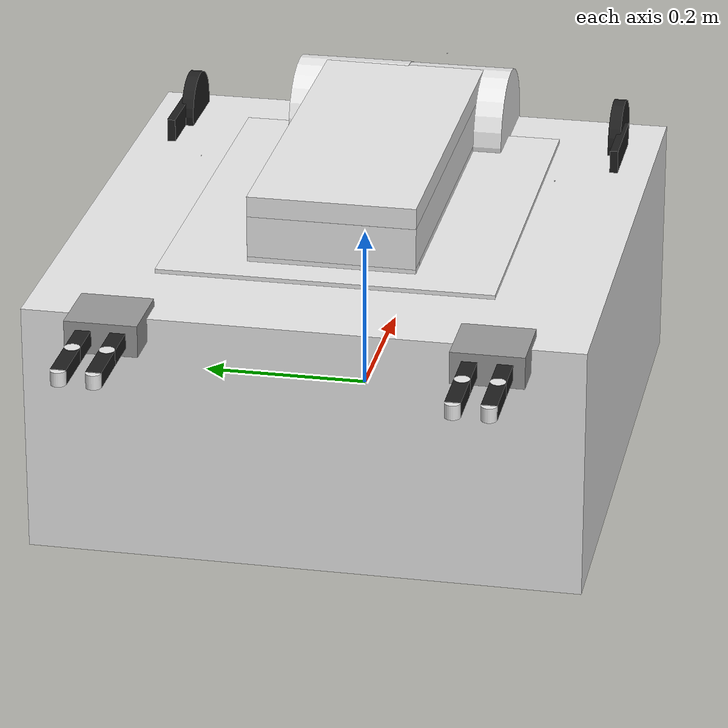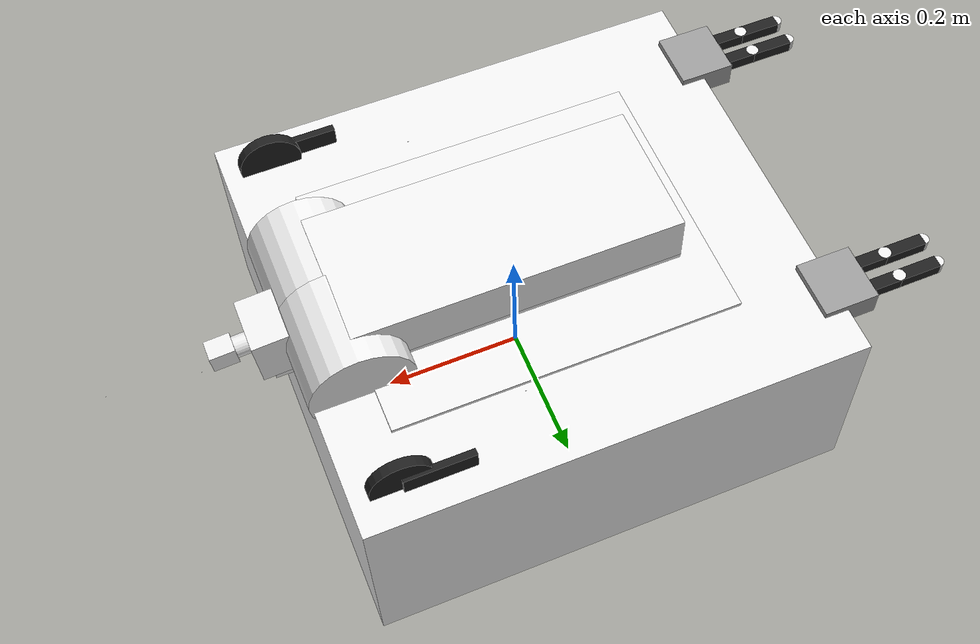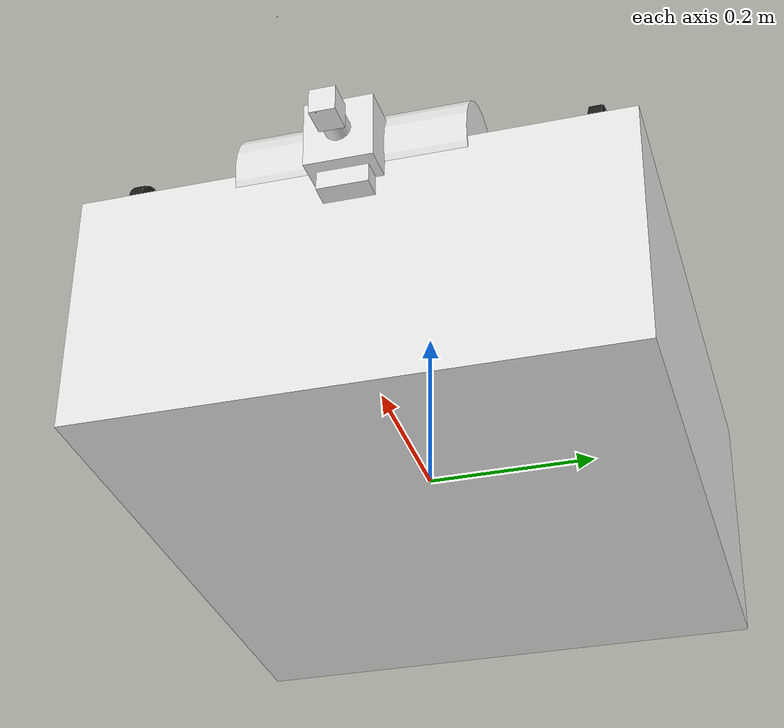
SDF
<sdf version='1.4'>
  <model name='sergio'>
    <link name='base_link'>
      <pose>0 0 0 0 -0 0</pose>
      <inertial>
        <pose>0.183413 -3.77114e-18 0.169408 0 -0 0</pose>
        <mass>0.92</mass>
        <inertia>
          <ixx>0.0232844</ixx>
          <ixy>-6.36342e-19</ixy>
          <ixz>-0.00704276</ixz>
          <iyy>0.0329244</iyy>
          <iyz>-2.92848e-19</iyz>
          <izz>0.0454683</izz>
        </inertia>
      </inertial>
      <collision name='base_link_collision'>
        <pose>0 0 0 0 -0 0</pose>
        <geometry>
          <cylinder>
            <length>0</length>
            <radius>0</radius>
          </cylinder>
        </geometry>
        <surface>
          <contact>
            <ode/>
          </contact>
          <friction>
            <ode/>
          </friction>
        </surface>
        <surface>
          <contact>
            <ode/>
          </contact>
          <friction>
            <ode/>
          </friction>
        </surface>
      </collision>
      <collision name='base_link_collision_base'>
        <pose>-0.0235 0 0.085 0 -0 0</pose>
        <geometry>
          <box>
            <size>0.713 0.65 0.3</size>
          </box>
        </geometry>
        <surface>
          <contact>
            <ode/>
          </contact>
          <friction>
            <ode/>
          </friction>
        </surface>
        <surface>
          <contact>
            <ode/>
          </contact>
          <friction>
            <ode/>
          </friction>
        </surface>
        <surface>
          <contact>
            <ode/>
          </contact>
          <friction>
            <ode/>
          </friction>
        </surface>
      </collision>
      <collision name='base_link_collision_base_laser'>
        <pose>0.3295 0 0.2095 0 -0 0</pose>
        <geometry>
          <box>
            <size>0.06 0.06 0.069</size>
          </box>
        </geometry>
        <surface>
          <contact>
            <ode/>
          </contact>
          <friction>
            <ode/>
          </friction>
        </surface>
        <surface>
          <contact>
            <ode/>
          </contact>
          <friction>
            <ode/>
          </friction>
        </surface>
        <surface>
          <contact>
            <ode/>
          </contact>
          <friction>
            <ode/>
          </friction>
        </surface>
      </collision>
      <collision name='base_link_collision_base_lasertop'>
        <pose>0.3295 0 0.253 0 -0 0</pose>
        <geometry>
          <box>
            <size>0.06 0.06 0.018</size>
          </box>
        </geometry>
        <surface>
          <contact>
            <ode/>
          </contact>
          <friction>
            <ode/>
          </friction>
        </surface>
        <surface>
          <contact>
            <ode/>
          </contact>
          <friction>
            <ode/>
          </friction>
        </surface>
        <surface>
          <contact>
            <ode/>
          </contact>
          <friction>
            <ode/>
          </friction>
        </surface>
      </collision>
      <collision name='base_link_collision_base_torso_mount'>
        <pose>0 0 0.14 0 -0 0</pose>
        <geometry>
          <cylinder>
            <length>0</length>
            <radius>0</radius>
          </cylinder>
        </geometry>
        <surface>
          <contact>
            <ode/>
          </contact>
          <friction>
            <ode/>
          </friction>
        </surface>
        <surface>
          <contact>
            <ode/>
          </contact>
          <friction>
            <ode/>
          </friction>
        </surface>
        <surface>
          <contact>
            <ode/>
          </contact>
          <friction>
            <ode/>
          </friction>
        </surface>
      </collision>
      <collision name='base_link_collision_laser_mount'>
        <pose>0.3045 0 0.1575 0 -0 0</pose>
        <geometry>
          <box>
            <size>0.01 0.06 0.035</size>
          </box>
        </geometry>
        <surface>
          <contact>
            <ode/>
          </contact>
          <friction>
            <ode/>
          </friction>
        </surface>
        <surface>
          <contact>
            <ode/>
          </contact>
          <friction>
            <ode/>
          </friction>
        </surface>
        <surface>
          <contact>
            <ode/>
          </contact>
          <friction>
            <ode/>
          </friction>
        </surface>
      </collision>
      <collision name='base_link_collision_sidepot_left'>
        <pose>0 0.28075 0.085 0 -0 0</pose>
        <geometry>
          <box>
            <size>0.4 0.0615 0.1</size>
          </box>
        </geometry>
        <surface>
          <contact>
            <ode/>
          </contact>
          <friction>
            <ode/>
          </friction>
        </surface>
        <surface>
          <contact>
            <ode/>
          </contact>
          <friction>
            <ode/>
          </friction>
        </surface>
        <surface>
          <contact>
            <ode/>
          </contact>
          <friction>
            <ode/>
          </friction>
        </surface>
      </collision>
      <collision name='base_link_collision_sidepot_right'>
        <pose>0 -0.28075 0.085 0 -0 0</pose>
        <geometry>
          <box>
            <size>0.4 0.0615 0.1</size>
          </box>
        </geometry>
        <surface>
          <contact>
            <ode/>
          </contact>
          <friction>
            <ode/>
          </friction>
        </surface>
        <surface>
          <contact>
            <ode/>
          </contact>
          <friction>
            <ode/>
          </friction>
        </surface>
        <surface>
          <contact>
            <ode/>
          </contact>
          <friction>
            <ode/>
          </friction>
        </surface>
      </collision>
      <collision name='base_link_collision_torso_mounting_frame'>
        <pose>0 0 0.215 0 -0 0</pose>
        <geometry>
          <box>
            <size>0.5 0.4 0.05</size>
          </box>
        </geometry>
        <surface>
          <contact>
            <ode/>
          </contact>
          <friction>
            <ode/>
          </friction>
        </surface>
        <surface>
          <contact>
            <ode/>
          </contact>
          <friction>
            <ode/>
          </friction>
        </surface>
        <surface>
          <contact>
            <ode/>
          </contact>
          <friction>
            <ode/>
          </friction>
        </surface>
      </collision>
      <visual name='base_link_visual'>
        <pose>0 0 0 0 -0 0</pose>
        <geometry>
          <cylinder>
            <length>0</length>
            <radius>0</radius>
          </cylinder>
        </geometry>
        <material>
          <script>
            <name>Gazebo/White</name>
            <uri>__default__</uri>
          </script>
        </material>
        <material>
          <script>
            <name>Gazebo/White</name>
            <uri>__default__</uri>
          </script>
        </material>
      </visual>
      <visual name='base_link_visual_base'>
        <pose>-0.0235 0 0.085 0 -0 0</pose>
        <geometry>
          <box>
            <size>0.713 0.65 0.3</size>
          </box>
        </geometry>
        <material>
          <script>
            <name>Gazebo/White</name>
            <uri>__default__</uri>
          </script>
        </material>
      </visual>
      <visual name='base_link_visual_base_laser'>
        <pose>0.3295 0 0.2095 0 -0 0</pose>
        <geometry>
          <box>
            <size>0.06 0.06 0.069</size>
          </box>
        </geometry>
        <material>
          <script>
            <name>Gazebo/White</name>
            <uri>__default__</uri>
          </script>
        </material>
        <material>
          <script>
            <name>Gazebo/Black</name>
            <uri>__default__</uri>
          </script>
        </material>
      </visual>
      <visual name='base_link_visual_base_lasertop'>
        <pose>0.3295 0 0.253 0 -0 0</pose>
        <geometry>
          <box>
            <size>0.06 0.06 0.018</size>
          </box>
        </geometry>
        <material>
          <script>
            <name>Gazebo/White</name>
            <uri>__default__</uri>
          </script>
        </material>
        <material>
          <script>
            <name>Gazebo/Black</name>
            <uri>__default__</uri>
          </script>
        </material>
        <material>
          <script>
            <name>Gazebo/Orange</name>
            <uri>__default__</uri>
          </script>
        </material>
      </visual>
      <visual name='base_link_visual_base_torso_mount'>
        <pose>0 0 0.14 0 -0 0</pose>
        <geometry>
          <cylinder>
            <length>0</length>
            <radius>0</radius>
          </cylinder>
        </geometry>
        <material>
          <script>
            <name>Gazebo/White</name>
            <uri>__default__</uri>
          </script>
        </material>
        <material>
          <script>
            <name>Gazebo/White</name>
            <uri>__default__</uri>
          </script>
        </material>
      </visual>
      <visual name='base_link_visual_laser_mount'>
        <pose>0.3045 0 0.1575 0 -0 0</pose>
        <geometry>
          <box>
            <size>0.01 0.06 0.035</size>
          </box>
        </geometry>
        <material>
          <script>
            <name>Gazebo/White</name>
            <uri>__default__</uri>
          </script>
        </material>
      </visual>
      <visual name='base_link_visual_sidepot_left'>
        <pose>0 0.28075 0.085 0 -0 0</pose>
        <geometry>
          <box>
            <size>0.4 0.0615 0.1</size>
          </box>
        </geometry>
        <material>
          <script>
            <name>Gazebo/White</name>
            <uri>__default__</uri>
          </script>
        </material>
      </visual>
      <visual name='base_link_visual_sidepot_right'>
        <pose>0 -0.28075 0.085 0 -0 0</pose>
        <geometry>
          <box>
            <size>0.4 0.0615 0.1</size>
          </box>
        </geometry>
        <material>
          <script>
            <name>Gazebo/White</name>
            <uri>__default__</uri>
          </script>
        </material>
      </visual>
      <visual name='base_link_visual_torso_mounting_frame'>
        <pose>0 0 0.215 0 -0 0</pose>
        <geometry>
          <box>
            <size>0.5 0.4 0.05</size>
          </box>
        </geometry>
        <material>
          <script>
            <name>Gazebo/White</name>
            <uri>__default__</uri>
          </script>
        </material>
      </visual>
      <velocity_decay>
        <linear>0</linear>
        <angular>0</angular>
      </velocity_decay>
      <velocity_decay>
        <linear>0</linear>
        <angular>0</angular>
      </velocity_decay>
      <sensor name='base_kinect_openni_camera' type='depth'>
        <update_rate>20</update_rate>
        <camera name='base_kinect'>
          <horizontal_fov>1.0472</horizontal_fov>
          <image>
            <width>640</width>
            <height>480</height>
            <format>R8G8B8</format>
          </image>
          <clip>
            <near>0.05</near>
            <far>3</far>
          </clip>
        </camera>
        <plugin name='base_kinect_camera_controller' filename='libKinectPlugin.so'>
          <alwaysOn>1</alwaysOn>
          <updateRate>20</updateRate>
          <cameraName>base_kinect</cameraName>
          <imageTopicName>rgb/image_color</imageTopicName>
          <cameraInfoTopicName>rgb/camera_info</cameraInfoTopicName>
          <depthImageTopicName>depth/image</depthImageTopicName>
          <depthImageCameraInfoTopicName>depth/camera_info</depthImageCameraInfoTopicName>
          <pointCloudTopicName>rgb/points</pointCloudTopicName>
          <frameName>base_kinect/openni_depth_optical_frame</frameName>
        </plugin>
        <pose>0.3 0 0.315 0 -0.07 0</pose>
      </sensor>
      <sensor name='base_ray_sensor' type='ray'>
        <update_rate>100</update_rate>
        <ray>
          <scan>
            <horizontal>
              <samples>918</samples>
              <resolution>1</resolution>
              <min_angle>-2.00277</min_angle>
              <max_angle>1.9984</max_angle>
            </horizontal>
            <vertical>
              <samples>1</samples>
              <min_angle>0</min_angle>
              <max_angle>0</max_angle>
            </vertical>
          </scan>
          <range>
            <min>0.05</min>
            <max>60</max>
            <resolution>0.01</resolution>
          </range>
        </ray>
        <plugin name='base_ros_ray_sensor_controller' filename='libLaserPlugin.so'>
          <gaussianNoise>0.005</gaussianNoise>
          <alwaysOn>1</alwaysOn>
          <updateRate>40</updateRate>
          <topicName>base_front_laser</topicName>
          <node_namespace>base</node_namespace>
          <frameName>base_laser</frameName>
        </plugin>
        <pose>0.3295 0 0.23 0 -0 0</pose>
      </sensor>
      <velocity_decay>
        <linear>0</linear>
        <angular>0</angular>
      </velocity_decay>
      <velocity_decay>
        <linear>0</linear>
        <angular>0</angular>
      </velocity_decay>
      <velocity_decay>
        <linear>0</linear>
        <angular>0</angular>
      </velocity_decay>
      <velocity_decay>
        <linear>0</linear>
        <angular>0</angular>
      </velocity_decay>
      <velocity_decay>
        <linear>0</linear>
        <angular>0</angular>
      </velocity_decay>
      <velocity_decay>
        <linear>0</linear>
        <angular>0</angular>
      </velocity_decay>
      <velocity_decay>
        <linear>0</linear>
        <angular>0</angular>
      </velocity_decay>
      <gravity>1</gravity>
      <velocity_decay>
        <linear>0</linear>
        <angular>0</angular>
      </velocity_decay>
      <self_collide>0</self_collide>
    </link>
    <link name='lower_rear_leg'>
      <pose>-0.185 0 0.2465 0 -0 0</pose>
      <inertial>
        <pose>0.195 0 0 0 -0 0</pose>
        <mass>5</mass>
        <inertia>
          <ixx>0.001</ixx>
          <ixy>0</ixy>
          <ixz>0</ixz>
          <iyy>0.001</iyy>
          <iyz>0</iyz>
          <izz>0.001</izz>
        </inertia>
      </inertial>
      <collision name='lower_rear_leg_collision'>
        <pose>0.195 0 0 0 -0 0</pose>
        <geometry>
          <box>
            <size>0.39 0.2 0.05</size>
          </box>
        </geometry>
        <surface>
          <contact>
            <ode/>
          </contact>
          <friction>
            <ode/>
          </friction>
        </surface>
      </collision>
      <visual name='lower_rear_leg_visual'>
        <pose>0.195 0 0 0 -0 0</pose>
        <geometry>
          <box>
            <size>0.39 0.2 0.05</size>
          </box>
        </geometry>
        <material>
          <script>
            <name>Gazebo/White</name>
            <uri>__default__</uri>
          </script>
        </material>
      </visual>
      <gravity>1</gravity>
      <velocity_decay>
        <linear>0</linear>
        <angular>0</angular>
      </velocity_decay>
      <self_collide>0</self_collide>
    </link>
    <joint name='ankle_joint' type='revolute'>
      <child>lower_rear_leg</child>
      <parent>base_link</parent>
      <axis>
        <xyz>0 -1 0</xyz>
        <limit>
          <lower>0.152</lower>
          <upper>1</upper>
          <effort>1000</effort>
          <velocity>0.265</velocity>
        </limit>
        <dynamics>
          <damping>6</damping>
        </dynamics>
      </axis>
    </joint>
    <link name='upper_leg'>
      <pose>0.205 0 0.2465 -0.00159265 0.00159265 3.14159</pose>
      <inertial>
        <pose>0.20575 0 0 0 -0 0</pose>
        <mass>5</mass>
        <inertia>
          <ixx>0.001</ixx>
          <ixy>0</ixy>
          <ixz>0</ixz>
          <iyy>0.001</iyy>
          <iyz>0</iyz>
          <izz>0.001</izz>
        </inertia>
      </inertial>
      <collision name='upper_leg_collision'>
        <pose>0.20575 0 0 0 -0 0</pose>
        <geometry>
          <box>
            <size>0.4115 0.2 0.1</size>
          </box>
        </geometry>
        <surface>
          <contact>
            <ode/>
          </contact>
          <friction>
            <ode/>
          </friction>
        </surface>
      </collision>
      <visual name='upper_leg_visual'>
        <pose>0.20575 0 0 0 -0 0</pose>
        <geometry>
          <box>
            <size>0.4115 0.2 0.1</size>
          </box>
        </geometry>
        <material>
          <script>
            <name>Gazebo/White</name>
            <uri>__default__</uri>
          </script>
        </material>
      </visual>
      <gravity>1</gravity>
      <velocity_decay>
        <linear>0</linear>
        <angular>0</angular>
      </velocity_decay>
      <self_collide>0</self_collide>
    </link>
    <joint name='knee_joint' type='revolute'>
      <child>upper_leg</child>
      <parent>lower_rear_leg</parent>
      <axis>
        <xyz>-2.53654e-06 0.999999 0.00159265</xyz>
        <limit>
          <lower>0.419</lower>
          <upper>2.059</upper>
          <effort>1000</effort>
          <velocity>0.539</velocity>
        </limit>
        <dynamics>
          <damping>6</damping>
        </dynamics>
      </axis>
    </joint>
    <link name='trunk'>
      <pose>-0.206499 -5.29396e-23 0.245845 -2.01992e-09 -2.01992e-09 2.53654e-06</pose>
      <inertial>
        <pose>0.243359 0 -3.32841e-05 0 -0 0</pose>
        <mass>10.35</mass>
        <inertia>
          <ixx>0.0223699</ixx>
          <ixy>0</ixy>
          <ixz>0.000107463</ixz>
          <iyy>0.0420765</iyy>
          <iyz>-4.81381e-06</iyz>
          <izz>0.0433416</izz>
        </inertia>
      </inertial>
      <collision name='trunk_collision'>
        <pose>0.235 0 0 0 -0 0</pose>
        <geometry>
          <box>
            <size>0.47 0.2 0.15</size>
          </box>
        </geometry>
        <surface>
          <contact>
            <ode/>
          </contact>
          <friction>
            <ode/>
          </friction>
        </surface>
      </collision>
      <collision name='trunk_collision_head_mount'>
        <pose>0.555307 4.23516e-22 -0.00688981 3.14 0.065 0</pose>
        <geometry>
          <box>
            <size>0.061 0.08 0.08</size>
          </box>
        </geometry>
        <surface>
          <contact>
            <ode/>
          </contact>
          <friction>
            <ode/>
          </friction>
        </surface>
        <surface>
          <contact>
            <ode/>
          </contact>
          <friction>
            <ode/>
          </friction>
        </surface>
      </collision>
      <collision name='trunk_collision_shoulder_mount_left'>
        <pose>0.47 0.0650002 0.000246861 -1.57319 -0 0</pose>
        <geometry>
          <cylinder>
            <length>0.14</length>
            <radius>0.075</radius>
          </cylinder>
        </geometry>
        <surface>
          <contact>
            <ode/>
          </contact>
          <friction>
            <ode/>
          </friction>
        </surface>
        <surface>
          <contact>
            <ode/>
          </contact>
          <friction>
            <ode/>
          </friction>
        </surface>
      </collision>
      <collision name='trunk_collision_shoulder_mount_right'>
        <pose>0.47 -0.0650002 -0.000246861 -1.57319 -0 0</pose>
        <geometry>
          <cylinder>
            <length>0.14</length>
            <radius>0.075</radius>
          </cylinder>
        </geometry>
        <surface>
          <contact>
            <ode/>
          </contact>
          <friction>
            <ode/>
          </friction>
        </surface>
        <surface>
          <contact>
            <ode/>
          </contact>
          <friction>
            <ode/>
          </friction>
        </surface>
      </collision>
      <visual name='trunk_visual'>
        <pose>0.235 0 0 0 -0 0</pose>
        <geometry>
          <box>
            <size>0.47 0.2 0.15</size>
          </box>
        </geometry>
        <material>
          <script>
            <name>Gazebo/White</name>
            <uri>__default__</uri>
          </script>
        </material>
      </visual>
      <visual name='trunk_visual_head_mount'>
        <pose>0.555307 4.23516e-22 -0.00688981 3.14 0.065 0</pose>
        <geometry>
          <box>
            <size>0.061 0.08 0.08</size>
          </box>
        </geometry>
        <material>
          <script>
            <name>Gazebo/White</name>
            <uri>__default__</uri>
          </script>
        </material>
        <material>
          <script>
            <name>Gazebo/White</name>
            <uri>__default__</uri>
          </script>
        </material>
      </visual>
      <visual name='trunk_visual_shoulder_mount_left'>
        <pose>0.47 0.0650002 0.000246861 -1.57319 -0 0</pose>
        <geometry>
          <cylinder>
            <length>0.14</length>
            <radius>0.075</radius>
          </cylinder>
        </geometry>
        <material>
          <script>
            <name>Gazebo/White</name>
            <uri>__default__</uri>
          </script>
        </material>
      </visual>
      <visual name='trunk_visual_shoulder_mount_right'>
        <pose>0.47 -0.0650002 -0.000246861 -1.57319 -0 0</pose>
        <geometry>
          <cylinder>
            <length>0.14</length>
            <radius>0.075</radius>
          </cylinder>
        </geometry>
        <material>
          <script>
            <name>Gazebo/White</name>
            <uri>__default__</uri>
          </script>
        </material>
      </visual>
      <velocity_decay>
        <linear>0</linear>
        <angular>0</angular>
      </velocity_decay>
      <velocity_decay>
        <linear>0</linear>
        <angular>0</angular>
      </velocity_decay>
      <velocity_decay>
        <linear>0</linear>
        <angular>0</angular>
      </velocity_decay>
      <gravity>1</gravity>
      <velocity_decay>
        <linear>0</linear>
        <angular>0</angular>
      </velocity_decay>
      <self_collide>0</self_collide>
    </link>
    <joint name='hip_joint' type='revolute'>
      <child>trunk</child>
      <parent>upper_leg</parent>
      <axis>
        <xyz>2.53654e-06 -1 2.01992e-09</xyz>
        <limit>
          <lower>1.007</lower>
          <upper>2.31</upper>
          <effort>1000</effort>
          <velocity>0.375</velocity>
        </limit>
        <dynamics>
          <damping>6</damping>
        </dynamics>
      </axis>
    </joint>
    <link name='neck_pan'>
      <pose>0.399201 1.53636e-06 0.235675 -3.11872 1.50577 -3.11708</pose>
      <inertial>
        <pose>0 0 -0.01 0 -0 0</pose>
        <mass>0.05</mass>
        <inertia>
          <ixx>0.0001</ixx>
          <ixy>0</ixy>
          <ixz>0</ixz>
          <iyy>0.0001</iyy>
          <iyz>0</iyz>
          <izz>0.0001</izz>
        </inertia>
      </inertial>
      <collision name='neck_pan_collision'>
        <pose>0 0 -0.01 0 -0 0</pose>
        <geometry>
          <cylinder>
            <length>0.02</length>
            <radius>0.015</radius>
          </cylinder>
        </geometry>
        <surface>
          <contact>
            <ode/>
          </contact>
          <friction>
            <ode/>
          </friction>
        </surface>
      </collision>
      <visual name='neck_pan_visual'>
        <pose>0 0 -0.01 0 -0 0</pose>
        <geometry>
          <cylinder>
            <length>0.02</length>
            <radius>0.015</radius>
          </cylinder>
        </geometry>
        <material>
          <script>
            <name>Gazebo/White</name>
            <uri>__default__</uri>
          </script>
        </material>
      </visual>
      <gravity>1</gravity>
      <velocity_decay>
        <linear>0</linear>
        <angular>0</angular>
      </velocity_decay>
      <self_collide>0</self_collide>
    </link>
    <joint name='neck_pan_joint' type='revolute'>
      <child>neck_pan</child>
      <parent>trunk</parent>
      <axis>
        <xyz>0.997887 0.00159518 -0.0649604</xyz>
        <limit>
          <lower>-1.586</lower>
          <upper>1.586</upper>
          <effort>13.4</effort>
          <velocity>1</velocity>
        </limit>
        <dynamics>
          <damping>0.1</damping>
        </dynamics>
      </axis>
    </joint>
    <link name='neck_tilt'>
      <pose>0.399201 1.53636e-06 0.235675 -3.11872 1.50577 -3.11708</pose>
      <inertial>
        <pose>0.00945205 0.00257534 0.0290274 0 -0 0</pose>
        <mass>0.073</mass>
        <inertia>
          <ixx>0.00332243</ixx>
          <ixy>-3.86301e-06</ixy>
          <ixz>-1.65411e-05</ixz>
          <iyy>0.00333348</iyy>
          <iyz>-4.50685e-06</iyz>
          <izz>0.00331731</izz>
        </inertia>
      </inertial>
      <collision name='neck_tilt_collision'>
        <pose>0 -0 0.018 0 -0 0</pose>
        <geometry>
          <box>
            <size>0.03 0.03 0.036</size>
          </box>
        </geometry>
        <surface>
          <contact>
            <ode/>
          </contact>
          <friction>
            <ode/>
          </friction>
        </surface>
      </collision>
      <collision name='neck_tilt_collision_head'>
        <pose>0 0 0.177 0 0 -1.5708</pose>
        <geometry>
          <box>
            <size>0.001 0.001 0.001</size>
          </box>
        </geometry>
        <surface>
          <contact>
            <ode/>
          </contact>
          <friction>
            <ode/>
          </friction>
        </surface>
        <surface>
          <contact>
            <ode/>
          </contact>
          <friction>
            <ode/>
          </friction>
        </surface>
        <surface>
          <contact>
            <ode/>
          </contact>
          <friction>
            <ode/>
          </friction>
        </surface>
      </collision>
      <visual name='neck_tilt_visual'>
        <pose>0 -0 0.018 0 -0 0</pose>
        <geometry>
          <box>
            <size>0.03 0.03 0.036</size>
          </box>
        </geometry>
        <material>
          <script>
            <name>Gazebo/White</name>
            <uri>__default__</uri>
          </script>
        </material>
      </visual>
      <visual name='neck_tilt_visual_head'>
        <pose>0 0 0.177 0 0 -1.5708</pose>
        <geometry>
          <box>
            <size>0.001 0.001 0.001</size>
          </box>
        </geometry>
        <material>
          <script>
            <name>Gazebo/White</name>
            <uri>__default__</uri>
          </script>
        </material>
      </visual>
      <visual name='neck_tilt_visual_top_kinect/openni_camera'>
        <pose>0.03 0 0.053 0 -0 0</pose>
        <geometry>
          <mesh>
            <scale>1 1 1</scale>
            <uri>model://media/meshes/kinect_without_base.dae</uri>
          </mesh>
        </geometry>
      </visual>
      <velocity_decay>
        <linear>0</linear>
        <angular>0</angular>
      </velocity_decay>
      <velocity_decay>
        <linear>0</linear>
        <angular>0</angular>
      </velocity_decay>
      <gravity>1</gravity>
      <velocity_decay>
        <linear>0</linear>
        <angular>0</angular>
      </velocity_decay>
      <self_collide>0</self_collide>
      <sensor name='openni_camera' type='depth'>
        <update_rate>20</update_rate>
        <camera name='top_kinect'>
          <horizontal_fov>1.0472</horizontal_fov>
          <image>
            <width>640</width>
            <height>480</height>
            <format>R8G8B8</format>
          </image>
          <clip>
            <near>0.05</near>
            <far>3</far>
          </clip>
        </camera>
        <plugin name='kinect_camera_controller' filename='libKinectPlugin.so'>
          <alwaysOn>1</alwaysOn>
          <updateRate>20</updateRate>
          <cameraName>top_kinect</cameraName>
          <imageTopicName>rgb/image_color</imageTopicName>
          <cameraInfoTopicName>rgb/camera_info</cameraInfoTopicName>
          <depthImageTopicName>depth/image</depthImageTopicName>
          <depthImageCameraInfoTopicName>depth/camera_info</depthImageCameraInfoTopicName>
          <pointCloudTopicName>rgb/points</pointCloudTopicName>
          <frameName>top_kinect/openni_depth_optical_frame</frameName>
        </plugin>
        <pose>0 0 0.036 0 -0 0</pose>
      </sensor>
    </link>
    <joint name='neck_tilt_joint' type='revolute'>
      <child>neck_tilt</child>
      <parent>neck_pan</parent>
      <axis>
        <xyz>-0.00169528 0.999997 -0.00148583</xyz>
        <limit>
          <lower>-0.994</lower>
          <upper>0.994</upper>
          <effort>13.4</effort>
          <velocity>1</velocity>
        </limit>
        <dynamics>
          <damping>0.1</damping>
        </dynamics>
      </axis>
    </joint>
    <link name='torso_laser_mount'>
      <pose>0.109801 8.02173e-07 0.178745 3.14 1.406 2.5244e-06</pose>
      <inertial>
        <pose>0 0 -0.0285865 0 -0 0</pose>
        <mass>0.52</mass>
        <inertia>
          <ixx>0.000326884</ixx>
          <ixy>0</ixy>
          <ixz>0</ixz>
          <iyy>0.000326884</iyy>
          <iyz>0</iyz>
          <izz>0.0003</izz>
        </inertia>
      </inertial>
      <collision name='torso_laser_mount_collision'>
        <pose>0 0 0 0 -0 0</pose>
        <geometry>
          <box>
            <size>0 0 0</size>
          </box>
        </geometry>
        <surface>
          <contact>
            <ode/>
          </contact>
          <friction>
            <ode/>
          </friction>
        </surface>
      </collision>
      <collision name='torso_laser_mount_collision_torso_laser'>
        <pose>0 0 -0.03 0 -0 0</pose>
        <geometry>
          <box>
            <size>0.06 0.06 0.069</size>
          </box>
        </geometry>
        <surface>
          <contact>
            <ode/>
          </contact>
          <friction>
            <ode/>
          </friction>
        </surface>
        <surface>
          <contact>
            <ode/>
          </contact>
          <friction>
            <ode/>
          </friction>
        </surface>
      </collision>
      <collision name='torso_laser_mount_collision_torso_lasertop'>
        <pose>0 0 0.0135 0 -0 0</pose>
        <geometry>
          <box>
            <size>0.06 0.06 0.018</size>
          </box>
        </geometry>
        <surface>
          <contact>
            <ode/>
          </contact>
          <friction>
            <ode/>
          </friction>
        </surface>
        <surface>
          <contact>
            <ode/>
          </contact>
          <friction>
            <ode/>
          </friction>
        </surface>
      </collision>
      <visual name='torso_laser_mount_visual'>
        <pose>0 0 0 0 -0 0</pose>
        <geometry>
          <box>
            <size>0 0 0</size>
          </box>
        </geometry>
        <material>
          <script>
            <name>Gazebo/White</name>
            <uri>__default__</uri>
          </script>
        </material>
        <material>
          <script>
            <name>Gazebo/Black</name>
            <uri>__default__</uri>
          </script>
        </material>
        <material>
          <script>
            <name>Gazebo/Black</name>
            <uri>__default__</uri>
          </script>
        </material>
      </visual>
      <visual name='torso_laser_mount_visual_torso_laser'>
        <pose>0 0 -0.03 0 -0 0</pose>
        <geometry>
          <box>
            <size>0.06 0.06 0.069</size>
          </box>
        </geometry>
        <material>
          <script>
            <name>Gazebo/Black</name>
            <uri>__default__</uri>
          </script>
        </material>
      </visual>
      <visual name='torso_laser_mount_visual_torso_lasertop'>
        <pose>0 0 0.0135 0 -0 0</pose>
        <geometry>
          <box>
            <size>0.06 0.06 0.018</size>
          </box>
        </geometry>
        <material>
          <script>
            <name>Gazebo/Black</name>
            <uri>__default__</uri>
          </script>
        </material>
        <material>
          <script>
            <name>Gazebo/Orange</name>
            <uri>__default__</uri>
          </script>
        </material>
      </visual>
      <velocity_decay>
        <linear>0</linear>
        <angular>0</angular>
      </velocity_decay>
      <velocity_decay>
        <linear>0</linear>
        <angular>0</angular>
      </velocity_decay>
      <gravity>1</gravity>
      <velocity_decay>
        <linear>0</linear>
        <angular>0</angular>
      </velocity_decay>
      <self_collide>0</self_collide>
    </link>
    <joint name='laser_tilt_joint' type='revolute'>
      <child>torso_laser_mount</child>
      <parent>trunk</parent>
      <axis>
        <xyz>0.00157361 -0.999999 0.000261279</xyz>
        <limit>
          <lower>0</lower>
          <upper>0.324</upper>
          <effort>13.4</effort>
          <velocity>1</velocity>
        </limit>
        <dynamics>
          <damping>0.1</damping>
        </dynamics>
      </axis>
    </joint>
    <link name='shoulder_link1_left'>
      <pose>0.2635 0.220001 0.245845 -0.00230874 1.5692 -1.5731</pose>
      <inertial>
        <pose>0 0 0 0 -0 0</pose>
        <mass>0.25</mass>
        <inertia>
          <ixx>6</ixx>
          <ixy>0</ixy>
          <ixz>0</ixz>
          <iyy>0.01</iyy>
          <iyz>0</iyz>
          <izz>0.01</izz>
        </inertia>
      </inertial>
      <collision name='shoulder_link1_left_collision'>
        <pose>0 0 -0.0525 0 -0 0</pose>
        <geometry>
          <cylinder>
            <length>0.015</length>
            <radius>0.045</radius>
          </cylinder>
        </geometry>
        <surface>
          <contact>
            <ode/>
          </contact>
          <friction>
            <ode/>
          </friction>
        </surface>
      </collision>
      <visual name='shoulder_link1_left_visual'>
        <pose>0 0 -0.0525 0 -0 0</pose>
        <geometry>
          <cylinder>
            <length>0.015</length>
            <radius>0.045</radius>
          </cylinder>
        </geometry>
        <material>
          <script>
            <name>Gazebo/Black</name>
            <uri>__default__</uri>
          </script>
        </material>
      </visual>
      <gravity>1</gravity>
      <velocity_decay>
        <linear>0</linear>
        <angular>0</angular>
      </velocity_decay>
      <self_collide>0</self_collide>
    </link>
    <joint name='shoulder_yaw_joint_left' type='revolute'>
      <child>shoulder_link1_left</child>
      <parent>trunk</parent>
      <axis>
        <xyz>3.66715e-06 0.00159265 0.999999</xyz>
        <limit>
          <lower>-1.57</lower>
          <upper>0</upper>
          <effort>13.4</effort>
          <velocity>1</velocity>
        </limit>
        <dynamics>
          <damping>4</damping>
        </dynamics>
      </axis>
    </joint>
    <link name='shoulder_link2_left'>
      <pose>0.2635 0.220001 0.245845 -1.57311 1.5692 -1.5731</pose>
      <inertial>
        <pose>0 0 0 0 -0 0</pose>
        <mass>0.15</mass>
        <inertia>
          <ixx>0.01</ixx>
          <ixy>0</ixy>
          <ixz>0</ixz>
          <iyy>4.04</iyy>
          <iyz>0</iyz>
          <izz>0.001</izz>
        </inertia>
      </inertial>
      <collision name='shoulder_link2_left_collision'>
        <pose>0 0.06 -0.05 0 -0 0</pose>
        <geometry>
          <box>
            <size>0.035 0.01 0.1</size>
          </box>
        </geometry>
        <surface>
          <contact>
            <ode/>
          </contact>
          <friction>
            <ode/>
          </friction>
        </surface>
      </collision>
      <visual name='shoulder_link2_left_visual'>
        <pose>0 0.06 -0.05 0 -0 0</pose>
        <geometry>
          <box>
            <size>0.035 0.01 0.1</size>
          </box>
        </geometry>
        <material>
          <script>
            <name>Gazebo/Black</name>
            <uri>__default__</uri>
          </script>
        </material>
      </visual>
      <gravity>1</gravity>
      <velocity_decay>
        <linear>0</linear>
        <angular>0</angular>
      </velocity_decay>
      <self_collide>0</self_collide>
    </link>
    <joint name='shoulder_pitch_joint_left' type='revolute'>
      <child>shoulder_link2_left</child>
      <parent>shoulder_link1_left</parent>
      <axis>
        <xyz>9.88295e-06 -0.999999 0.00159265</xyz>
        <limit>
          <lower>-1.57</lower>
          <upper>1.57</upper>
          <effort>13.4</effort>
          <velocity>1</velocity>
        </limit>
        <dynamics>
          <damping>4</damping>
        </dynamics>
      </axis>
    </joint>
    <link name='upper_arm_left'>
      <pose>0.2635 0.220001 0.245845 -0.00230874 1.5692 -1.5731</pose>
      <inertial>
        <pose>0 -0.2 0 0 -0 0</pose>
        <mass>2.95</mass>
        <inertia>
          <ixx>0.027</ixx>
          <ixy>0</ixy>
          <ixz>0</ixz>
          <iyy>0.45993</iyy>
          <iyz>0</iyz>
          <izz>0.004</izz>
        </inertia>
      </inertial>
      <collision name='upper_arm_left_collision'>
        <pose>-0.00959 -0.19131 -1e-05 0 -0 3.1415</pose>
        <geometry>
          <mesh>
            <scale>0.0004 0.0004 0.0004</scale>
            <uri>model://media/meshes/upperarmtextured.dae</uri>
          </mesh>
        </geometry>
        <surface>
          <contact>
            <ode/>
          </contact>
          <friction>
            <ode/>
          </friction>
        </surface>
      </collision>
      <visual name='upper_arm_left_visual'>
        <pose>-0.00959 -0.19131 -1e-05 0 -0 3.1415</pose>
        <geometry>
          <mesh>
            <scale>0.0004 0.0004 0.0004</scale>
            <uri>model://media/meshes/upperarmtextured.dae</uri>
          </mesh>
        </geometry>
        <material>
          <script>
            <name>sergio_description/white</name>
            <uri>__default__</uri>
          </script>
        </material>
      </visual>
      <gravity>1</gravity>
      <velocity_decay>
        <linear>0</linear>
        <angular>0</angular>
      </velocity_decay>
      <self_collide>0</self_collide>
    </link>
    <joint name='shoulder_roll_joint_left' type='revolute'>
      <child>upper_arm_left</child>
      <parent>shoulder_link2_left</parent>
      <axis>
        <xyz>-1 -6.20389e-06 3.67703e-06</xyz>
        <limit>
          <lower>-1.57</lower>
          <upper>1.57</upper>
          <effort>9.8</effort>
          <velocity>1</velocity>
        </limit>
        <dynamics>
          <damping>3.8</damping>
        </dynamics>
      </axis>
    </joint>
    <link name='elbow_link4_left'>
      <pose>-0.0565001 0.219983 0.235846 -1.57311 1.5692 -1.5731</pose>
      <inertial>
        <pose>0 0 0 0 -0 0</pose>
        <mass>0.1</mass>
        <inertia>
          <ixx>0.001</ixx>
          <ixy>0</ixy>
          <ixz>0</ixz>
          <iyy>0.6</iyy>
          <iyz>0</iyz>
          <izz>0.001</izz>
        </inertia>
      </inertial>
      <collision name='elbow_link4_left_collision'>
        <pose>0 0 0 0 -0 0</pose>
        <geometry>
          <cylinder>
            <length>0</length>
            <radius>0</radius>
          </cylinder>
        </geometry>
        <surface>
          <contact>
            <ode/>
          </contact>
          <friction>
            <ode/>
          </friction>
        </surface>
      </collision>
      <visual name='elbow_link4_left_visual'>
        <pose>0 0 0 0 -0 0</pose>
        <geometry>
          <cylinder>
            <length>0</length>
            <radius>0</radius>
          </cylinder>
        </geometry>
        <material>
          <script>
            <name>Gazebo/Grey</name>
            <uri>__default__</uri>
          </script>
        </material>
      </visual>
      <gravity>1</gravity>
      <velocity_decay>
        <linear>0</linear>
        <angular>0</angular>
      </velocity_decay>
      <self_collide>0</self_collide>
    </link>
    <joint name='elbow_pitch_joint_left' type='revolute'>
      <child>elbow_link4_left</child>
      <parent>upper_arm_left</parent>
      <axis>
        <xyz>9.88295e-06 -0.999999 0.00159265</xyz>
        <limit>
          <lower>0</lower>
          <upper>2.23</upper>
          <effort>4.5</effort>
          <velocity>1</velocity>
        </limit>
        <dynamics>
          <damping>3</damping>
        </dynamics>
      </axis>
    </joint>
    <link name='fore_arm_left'>
      <pose>-0.0565001 0.219983 0.235846 -0.00230874 1.5692 -1.5731</pose>
      <inertial>
        <pose>0 -0.14 0 0 -0 0</pose>
        <mass>0.85</mass>
        <inertia>
          <ixx>0.001</ixx>
          <ixy>0</ixy>
          <ixz>0</ixz>
          <iyy>0.5</iyy>
          <iyz>0</iyz>
          <izz>0.001</izz>
        </inertia>
      </inertial>
      <collision name='fore_arm_left_collision'>
        <pose>0.00425 -0.14868 0.00547 3.14159 -1.57079 3.14159</pose>
        <geometry>
          <mesh>
            <scale>0.0004 0.0004 0.0004</scale>
            <uri>model://media/meshes/forearmtextured.dae</uri>
          </mesh>
        </geometry>
        <surface>
          <contact>
            <ode/>
          </contact>
          <friction>
            <ode/>
          </friction>
        </surface>
      </collision>
      <visual name='fore_arm_left_visual'>
        <pose>0.00425 -0.14868 0.00547 3.14159 -1.57079 3.14159</pose>
        <geometry>
          <mesh>
            <scale>0.0004 0.0004 0.0004</scale>
            <uri>model://media/meshes/forearmtextured.dae</uri>
          </mesh>
        </geometry>
        <material>
          <script>
            <name>sergio_description/white</name>
            <uri>__default__</uri>
          </script>
        </material>
      </visual>
      <gravity>1</gravity>
      <velocity_decay>
        <linear>0</linear>
        <angular>0</angular>
      </velocity_decay>
      <self_collide>0</self_collide>
    </link>
    <joint name='elbow_roll_joint_left' type='revolute'>
      <child>fore_arm_left</child>
      <parent>elbow_link4_left</parent>
      <axis>
        <xyz>-1 -6.20389e-06 3.67703e-06</xyz>
        <limit>
          <lower>-1.83</lower>
          <upper>1.83</upper>
          <effort>4.5</effort>
          <velocity>1</velocity>
        </limit>
        <dynamics>
          <damping>3.5</damping>
        </dynamics>
      </axis>
    </joint>
    <link name='wrist_link6_left'>
      <pose>-0.3365 0.219966 0.225847 -3.14 -7.35023e-06 -3.14159</pose>
      <inertial>
        <pose>0 0 0 0 -0 0</pose>
        <mass>0.01</mass>
        <inertia>
          <ixx>0.001</ixx>
          <ixy>0</ixy>
          <ixz>0</ixz>
          <iyy>0.03322</iyy>
          <iyz>0</iyz>
          <izz>0.001</izz>
        </inertia>
      </inertial>
      <collision name='wrist_link6_left_collision'>
        <pose>0 0 0 1.5708 -0 0</pose>
        <geometry>
          <cylinder>
            <length>0</length>
            <radius>0</radius>
          </cylinder>
        </geometry>
        <surface>
          <contact>
            <ode/>
          </contact>
          <friction>
            <ode/>
          </friction>
        </surface>
      </collision>
      <visual name='wrist_link6_left_visual'>
        <pose>0 0 0 1.5708 -0 0</pose>
        <geometry>
          <cylinder>
            <length>0</length>
            <radius>0</radius>
          </cylinder>
        </geometry>
        <material>
          <script>
            <name>Gazebo/Black</name>
            <uri>__default__</uri>
          </script>
        </material>
      </visual>
      <gravity>1</gravity>
      <velocity_decay>
        <linear>0</linear>
        <angular>0</angular>
      </velocity_decay>
      <self_collide>0</self_collide>
    </link>
    <joint name='wrist_pitch_joint_left' type='revolute'>
      <child>wrist_link6_left</child>
      <parent>fore_arm_left</parent>
      <axis>
        <xyz>6.20972e-06 -0.999999 0.00158898</xyz>
        <limit>
          <lower>-0.95</lower>
          <upper>0.95</upper>
          <effort>1</effort>
          <velocity>1</velocity>
        </limit>
        <dynamics>
          <damping>0.35</damping>
        </dynamics>
      </axis>
    </joint>
    <link name='hand_left'>
      <pose>-0.3365 0.219966 0.225847 -3.14 -7.35023e-06 -3.14159</pose>
      <inertial>
        <pose>0.047619 0 0 0 -0 0</pose>
        <mass>0.21</mass>
        <inertia>
          <ixx>0.0101</ixx>
          <ixy>0</ixy>
          <ixz>0</ixz>
          <iyy>0.0101006</iyy>
          <iyz>0</iyz>
          <izz>0.0623006</izz>
        </inertia>
      </inertial>
      <collision name='hand_left_collision'>
        <pose>0.048 0 0 0 -0 0</pose>
        <geometry>
          <box>
            <size>0.08 0.085 0.038</size>
          </box>
        </geometry>
        <surface>
          <contact>
            <ode/>
          </contact>
          <friction>
            <ode/>
          </friction>
        </surface>
      </collision>
      <collision name='hand_left_collision_grippoint_left'>
        <pose>0.04 0 0 0 -0 0</pose>
        <geometry>
          <box>
            <size>0 0 0</size>
          </box>
        </geometry>
        <surface>
          <contact>
            <ode/>
          </contact>
          <friction>
            <ode/>
          </friction>
        </surface>
        <surface>
          <contact>
            <ode/>
          </contact>
          <friction>
            <ode/>
          </friction>
        </surface>
      </collision>
      <visual name='hand_left_visual'>
        <pose>0.048 0 0 0 -0 0</pose>
        <geometry>
          <box>
            <size>0.08 0.085 0.038</size>
          </box>
        </geometry>
        <material>
          <script>
            <name>Gazebo/Grey</name>
            <uri>__default__</uri>
          </script>
        </material>
      </visual>
      <visual name='hand_left_visual_grippoint_left'>
        <pose>0.04 0 0 0 -0 0</pose>
        <geometry>
          <box>
            <size>0 0 0</size>
          </box>
        </geometry>
        <material>
          <script>
            <name>Gazebo/Blue</name>
            <uri>__default__</uri>
          </script>
        </material>
      </visual>
      <velocity_decay>
        <linear>0</linear>
        <angular>0</angular>
      </velocity_decay>
      <gravity>1</gravity>
      <velocity_decay>
        <linear>0</linear>
        <angular>0</angular>
      </velocity_decay>
      <self_collide>0</self_collide>
    </link>
    <joint name='wrist_yaw_joint_left' type='revolute'>
      <child>hand_left</child>
      <parent>wrist_link6_left</parent>
      <axis>
        <xyz>7.41378e-06 0.00160487 1.01</xyz>
        <limit>
          <lower>-0.61</lower>
          <upper>0.61</upper>
          <effort>1</effort>
          <velocity>1</velocity>
        </limit>
        <dynamics>
          <damping>0.3</damping>
        </dynamics>
      </axis>
    </joint>
    <link name='finger1_left'>
      <pose>-0.4115 0.239965 0.225816 -2.03906 1.56902 -2.03905</pose>
      <inertial>
        <pose>0 0 -0.045 0 -0 0</pose>
        <mass>0.02</mass>
        <inertia>
          <ixx>0.0110045</ixx>
          <ixy>0</ixy>
          <ixz>1.05879e-22</ixz>
          <iyy>0.0110045</iyy>
          <iyz>0</iyz>
          <izz>0.011</izz>
        </inertia>
      </inertial>
      <collision name='finger1_left_collision'>
        <pose>0 0 -0.03 0 -0 0</pose>
        <geometry>
          <box>
            <size>0.018 0.018 0.06</size>
          </box>
        </geometry>
        <surface>
          <contact>
            <ode/>
          </contact>
          <friction>
            <ode/>
          </friction>
        </surface>
        <surface>
          <contact>
            <ode/>
          </contact>
          <friction>
            <ode>
              <mu>100</mu>
              <mu2>100</mu2>
            </ode>
          </friction>
        </surface>
      </collision>
      <collision name='finger1_left_collision_finger1_phalanx_left'>
        <pose>0 0 -0.06 0 1.57 0</pose>
        <geometry>
          <cylinder>
            <length>0.019</length>
            <radius>0.009</radius>
          </cylinder>
        </geometry>
        <surface>
          <contact>
            <ode/>
          </contact>
          <friction>
            <ode/>
          </friction>
        </surface>
        <surface>
          <contact>
            <ode/>
          </contact>
          <friction>
            <ode>
              <mu>100</mu>
              <mu2>100</mu2>
            </ode>
          </friction>
        </surface>
        <surface>
          <contact>
            <ode/>
          </contact>
          <friction>
            <ode/>
          </friction>
        </surface>
      </collision>
      <visual name='finger1_left_visual'>
        <pose>0 0 -0.03 0 -0 0</pose>
        <geometry>
          <box>
            <size>0.018 0.018 0.06</size>
          </box>
        </geometry>
        <material>
          <script>
            <name>Gazebo/Black</name>
            <uri>__default__</uri>
          </script>
        </material>
      </visual>
      <visual name='finger1_left_visual_finger1_phalanx_left'>
        <pose>0 0 -0.06 0 1.57 0</pose>
        <geometry>
          <cylinder>
            <length>0.019</length>
            <radius>0.009</radius>
          </cylinder>
        </geometry>
        <material>
          <script>
            <name>Gazebo/White</name>
            <uri>__default__</uri>
          </script>
        </material>
      </visual>
      <velocity_decay>
        <linear>0</linear>
        <angular>0</angular>
      </velocity_decay>
      <velocity_decay>
        <linear>0</linear>
        <angular>0</angular>
      </velocity_decay>
      <gravity>1</gravity>
      <velocity_decay>
        <linear>0</linear>
        <angular>0</angular>
      </velocity_decay>
      <self_collide>0</self_collide>
    </link>
    <joint name='finger1_joint_left' type='revolute'>
      <child>finger1_left</child>
      <parent>hand_left</parent>
      <axis>
        <xyz>-0.000803667 -0.00158899 -0.999998</xyz>
        <limit>
          <lower>-1.57</lower>
          <upper>1.57</upper>
          <effort>3</effort>
          <velocity>1</velocity>
        </limit>
        <dynamics>
          <damping>0.5</damping>
        </dynamics>
      </axis>
    </joint>
    <link name='finger1_tip_left'>
      <pose>-0.4715 0.239965 0.225864 -2.03906 1.56902 -2.03905</pose>
      <inertial>
        <pose>0 0 -0.045 0 -0 0</pose>
        <mass>0.02</mass>
        <inertia>
          <ixx>0.0013745</ixx>
          <ixy>0</ixy>
          <ixz>1.05879e-22</ixz>
          <iyy>0.0015245</iyy>
          <iyz>0</iyz>
          <izz>0.00152</izz>
        </inertia>
      </inertial>
      <collision name='finger1_tip_left_collision'>
        <pose>0 0 -0.03 0 -0 0</pose>
        <geometry>
          <box>
            <size>0.018 0.018 0.06</size>
          </box>
        </geometry>
        <surface>
          <contact>
            <ode/>
          </contact>
          <friction>
            <ode/>
          </friction>
        </surface>
        <surface>
          <contact>
            <ode/>
          </contact>
          <friction>
            <ode>
              <mu>100</mu>
              <mu2>100</mu2>
            </ode>
          </friction>
        </surface>
      </collision>
      <collision name='finger1_tip_left_collision_finger1_tip_phalanx_left'>
        <pose>0 0 -0.06 0 1.57 0</pose>
        <geometry>
          <cylinder>
            <length>0.017</length>
            <radius>0.009</radius>
          </cylinder>
        </geometry>
        <surface>
          <contact>
            <ode/>
          </contact>
          <friction>
            <ode/>
          </friction>
        </surface>
        <surface>
          <contact>
            <ode/>
          </contact>
          <friction>
            <ode>
              <mu>100</mu>
              <mu2>100</mu2>
            </ode>
          </friction>
        </surface>
        <surface>
          <contact>
            <ode/>
          </contact>
          <friction>
            <ode/>
          </friction>
        </surface>
      </collision>
      <visual name='finger1_tip_left_visual'>
        <pose>0 0 -0.03 0 -0 0</pose>
        <geometry>
          <box>
            <size>0.018 0.018 0.06</size>
          </box>
        </geometry>
        <material>
          <script>
            <name>Gazebo/Black</name>
            <uri>__default__</uri>
          </script>
        </material>
      </visual>
      <visual name='finger1_tip_left_visual_finger1_tip_phalanx_left'>
        <pose>0 0 -0.06 0 1.57 0</pose>
        <geometry>
          <cylinder>
            <length>0.017</length>
            <radius>0.009</radius>
          </cylinder>
        </geometry>
        <material>
          <script>
            <name>Gazebo/White</name>
            <uri>__default__</uri>
          </script>
        </material>
      </visual>
      <velocity_decay>
        <linear>0</linear>
        <angular>0</angular>
      </velocity_decay>
      <velocity_decay>
        <linear>0</linear>
        <angular>0</angular>
      </velocity_decay>
      <gravity>1</gravity>
      <velocity_decay>
        <linear>0</linear>
        <angular>0</angular>
      </velocity_decay>
      <self_collide>0</self_collide>
    </link>
    <joint name='finger1_tip_joint_left' type='revolute'>
      <child>finger1_tip_left</child>
      <parent>finger1_left</parent>
      <axis>
        <xyz>-0.000803667 -0.00158899 -0.999998</xyz>
        <limit>
          <lower>-1.57</lower>
          <upper>1.57</upper>
          <effort>3</effort>
          <velocity>1</velocity>
        </limit>
        <dynamics>
          <damping>0.5</damping>
        </dynamics>
      </axis>
    </joint>
    <link name='finger2_left'>
      <pose>-0.4115 0.199965 0.225879 -2.03906 1.56902 -2.03905</pose>
      <inertial>
        <pose>0 0 -0.045 0 -0 0</pose>
        <mass>0.02</mass>
        <inertia>
          <ixx>0.0110045</ixx>
          <ixy>0</ixy>
          <ixz>1.05879e-22</ixz>
          <iyy>0.0110045</iyy>
          <iyz>0</iyz>
          <izz>0.011</izz>
        </inertia>
      </inertial>
      <collision name='finger2_left_collision'>
        <pose>0 0 -0.03 0 -0 0</pose>
        <geometry>
          <box>
            <size>0.018 0.018 0.06</size>
          </box>
        </geometry>
        <surface>
          <contact>
            <ode/>
          </contact>
          <friction>
            <ode/>
          </friction>
        </surface>
        <surface>
          <contact>
            <ode/>
          </contact>
          <friction>
            <ode>
              <mu>100</mu>
              <mu2>100</mu2>
            </ode>
          </friction>
        </surface>
      </collision>
      <collision name='finger2_left_collision_finger2_phalanx_left'>
        <pose>0 0 -0.06 0 1.57 0</pose>
        <geometry>
          <cylinder>
            <length>0.019</length>
            <radius>0.009</radius>
          </cylinder>
        </geometry>
        <surface>
          <contact>
            <ode/>
          </contact>
          <friction>
            <ode/>
          </friction>
        </surface>
        <surface>
          <contact>
            <ode/>
          </contact>
          <friction>
            <ode>
              <mu>100</mu>
              <mu2>100</mu2>
            </ode>
          </friction>
        </surface>
        <surface>
          <contact>
            <ode/>
          </contact>
          <friction>
            <ode/>
          </friction>
        </surface>
      </collision>
      <visual name='finger2_left_visual'>
        <pose>0 0 -0.03 0 -0 0</pose>
        <geometry>
          <box>
            <size>0.018 0.018 0.06</size>
          </box>
        </geometry>
        <material>
          <script>
            <name>Gazebo/Black</name>
            <uri>__default__</uri>
          </script>
        </material>
      </visual>
      <visual name='finger2_left_visual_finger2_phalanx_left'>
        <pose>0 0 -0.06 0 1.57 0</pose>
        <geometry>
          <cylinder>
            <length>0.019</length>
            <radius>0.009</radius>
          </cylinder>
        </geometry>
        <material>
          <script>
            <name>Gazebo/White</name>
            <uri>__default__</uri>
          </script>
        </material>
      </visual>
      <velocity_decay>
        <linear>0</linear>
        <angular>0</angular>
      </velocity_decay>
      <velocity_decay>
        <linear>0</linear>
        <angular>0</angular>
      </velocity_decay>
      <gravity>1</gravity>
      <velocity_decay>
        <linear>0</linear>
        <angular>0</angular>
      </velocity_decay>
      <self_collide>0</self_collide>
    </link>
    <joint name='finger2_joint_left' type='revolute'>
      <child>finger2_left</child>
      <parent>hand_left</parent>
      <axis>
        <xyz>0.000803667 0.00158899 0.999998</xyz>
        <limit>
          <lower>-1.57</lower>
          <upper>1.57</upper>
          <effort>3</effort>
          <velocity>1</velocity>
        </limit>
        <dynamics>
          <damping>0.5</damping>
        </dynamics>
      </axis>
    </joint>
    <link name='finger2_tip_left'>
      <pose>-0.4715 0.199965 0.225927 -2.03906 1.56902 -2.03905</pose>
      <inertial>
        <pose>0 0 -0.045 0 -0 0</pose>
        <mass>0.02</mass>
        <inertia>
          <ixx>0.0013745</ixx>
          <ixy>0</ixy>
          <ixz>1.05879e-22</ixz>
          <iyy>0.0015245</iyy>
          <iyz>0</iyz>
          <izz>0.00152</izz>
        </inertia>
      </inertial>
      <collision name='finger2_tip_left_collision'>
        <pose>0 0 -0.03 0 -0 0</pose>
        <geometry>
          <box>
            <size>0.018 0.018 0.06</size>
          </box>
        </geometry>
        <surface>
          <contact>
            <ode/>
          </contact>
          <friction>
            <ode/>
          </friction>
        </surface>
        <surface>
          <contact>
            <ode/>
          </contact>
          <friction>
            <ode>
              <mu>100</mu>
              <mu2>100</mu2>
            </ode>
          </friction>
        </surface>
      </collision>
      <collision name='finger2_tip_left_collision_finger2_tip_phalanx_left'>
        <pose>0 0 -0.06 0 1.57 0</pose>
        <geometry>
          <cylinder>
            <length>0.017</length>
            <radius>0.009</radius>
          </cylinder>
        </geometry>
        <surface>
          <contact>
            <ode/>
          </contact>
          <friction>
            <ode/>
          </friction>
        </surface>
        <surface>
          <contact>
            <ode/>
          </contact>
          <friction>
            <ode>
              <mu>100</mu>
              <mu2>100</mu2>
            </ode>
          </friction>
        </surface>
        <surface>
          <contact>
            <ode/>
          </contact>
          <friction>
            <ode/>
          </friction>
        </surface>
      </collision>
      <visual name='finger2_tip_left_visual'>
        <pose>0 0 -0.03 0 -0 0</pose>
        <geometry>
          <box>
            <size>0.018 0.018 0.06</size>
          </box>
        </geometry>
        <material>
          <script>
            <name>Gazebo/Black</name>
            <uri>__default__</uri>
          </script>
        </material>
      </visual>
      <visual name='finger2_tip_left_visual_finger2_tip_phalanx_left'>
        <pose>0 0 -0.06 0 1.57 0</pose>
        <geometry>
          <cylinder>
            <length>0.017</length>
            <radius>0.009</radius>
          </cylinder>
        </geometry>
        <material>
          <script>
            <name>Gazebo/White</name>
            <uri>__default__</uri>
          </script>
        </material>
      </visual>
      <velocity_decay>
        <linear>0</linear>
        <angular>0</angular>
      </velocity_decay>
      <velocity_decay>
        <linear>0</linear>
        <angular>0</angular>
      </velocity_decay>
      <gravity>1</gravity>
      <velocity_decay>
        <linear>0</linear>
        <angular>0</angular>
      </velocity_decay>
      <self_collide>0</self_collide>
    </link>
    <joint name='finger2_tip_joint_left' type='revolute'>
      <child>finger2_tip_left</child>
      <parent>finger2_left</parent>
      <axis>
        <xyz>0.000803667 0.00158899 0.999998</xyz>
        <limit>
          <lower>-1.57</lower>
          <upper>1.57</upper>
          <effort>3</effort>
          <velocity>1</velocity>
        </limit>
        <dynamics>
          <damping>0.5</damping>
        </dynamics>
      </axis>
    </joint>
    <link name='shoulder_link1_right'>
      <pose>0.263501 -0.219999 0.245845 -0.00230874 1.5692 -1.5731</pose>
      <inertial>
        <pose>0 0 0 0 -0 0</pose>
        <mass>0.25</mass>
        <inertia>
          <ixx>6</ixx>
          <ixy>0</ixy>
          <ixz>0</ixz>
          <iyy>0.01</iyy>
          <iyz>0</iyz>
          <izz>0.01</izz>
        </inertia>
      </inertial>
      <collision name='shoulder_link1_right_collision'>
        <pose>0 0 0.0525 0 -0 0</pose>
        <geometry>
          <cylinder>
            <length>0.015</length>
            <radius>0.045</radius>
          </cylinder>
        </geometry>
        <surface>
          <contact>
            <ode/>
          </contact>
          <friction>
            <ode/>
          </friction>
        </surface>
      </collision>
      <visual name='shoulder_link1_right_visual'>
        <pose>0 0 0.0525 0 -0 0</pose>
        <geometry>
          <cylinder>
            <length>0.015</length>
            <radius>0.045</radius>
          </cylinder>
        </geometry>
        <material>
          <script>
            <name>Gazebo/Black</name>
            <uri>__default__</uri>
          </script>
        </material>
      </visual>
      <gravity>1</gravity>
      <velocity_decay>
        <linear>0</linear>
        <angular>0</angular>
      </velocity_decay>
      <self_collide>0</self_collide>
    </link>
    <joint name='shoulder_yaw_joint_right' type='revolute'>
      <child>shoulder_link1_right</child>
      <parent>trunk</parent>
      <axis>
        <xyz>-3.66715e-06 -0.00159265 -0.999999</xyz>
        <limit>
          <lower>-1.57</lower>
          <upper>0</upper>
          <effort>13.4</effort>
          <velocity>1</velocity>
        </limit>
        <dynamics>
          <damping>4</damping>
        </dynamics>
      </axis>
    </joint>
    <link name='shoulder_link2_right'>
      <pose>0.263501 -0.219999 0.245845 -1.57311 1.5692 -1.5731</pose>
      <inertial>
        <pose>0 0 0 0 -0 0</pose>
        <mass>0.15</mass>
        <inertia>
          <ixx>0.01</ixx>
          <ixy>0</ixy>
          <ixz>0</ixz>
          <iyy>4.04</iyy>
          <iyz>0</iyz>
          <izz>0.001</izz>
        </inertia>
      </inertial>
      <collision name='shoulder_link2_right_collision'>
        <pose>0 -0.06 -0.05 0 -0 0</pose>
        <geometry>
          <box>
            <size>0.035 0.01 0.1</size>
          </box>
        </geometry>
        <surface>
          <contact>
            <ode/>
          </contact>
          <friction>
            <ode/>
          </friction>
        </surface>
      </collision>
      <visual name='shoulder_link2_right_visual'>
        <pose>0 -0.06 -0.05 0 -0 0</pose>
        <geometry>
          <box>
            <size>0.035 0.01 0.1</size>
          </box>
        </geometry>
        <material>
          <script>
            <name>Gazebo/Black</name>
            <uri>__default__</uri>
          </script>
        </material>
      </visual>
      <gravity>1</gravity>
      <velocity_decay>
        <linear>0</linear>
        <angular>0</angular>
      </velocity_decay>
      <self_collide>0</self_collide>
    </link>
    <joint name='shoulder_pitch_joint_right' type='revolute'>
      <child>shoulder_link2_right</child>
      <parent>shoulder_link1_right</parent>
      <axis>
        <xyz>9.88295e-06 -0.999999 0.00159265</xyz>
        <limit>
          <lower>-1.57</lower>
          <upper>1.57</upper>
          <effort>13.4</effort>
          <velocity>1</velocity>
        </limit>
        <dynamics>
          <damping>4</damping>
        </dynamics>
      </axis>
    </joint>
    <link name='upper_arm_right'>
      <pose>0.263501 -0.219999 0.245845 -0.00230874 1.5692 -1.5731</pose>
      <inertial>
        <pose>0 -0.2 0 0 -0 0</pose>
        <mass>2.95</mass>
        <inertia>
          <ixx>0.027</ixx>
          <ixy>0</ixy>
          <ixz>0</ixz>
          <iyy>0.45993</iyy>
          <iyz>0</iyz>
          <izz>0.004</izz>
        </inertia>
      </inertial>
      <collision name='upper_arm_right_collision'>
        <pose>-0.00959 -0.19131 -1e-05 0 -0 3.1415</pose>
        <geometry>
          <mesh>
            <scale>0.0004 0.0004 0.0004</scale>
            <uri>model://media/meshes/upperarmtextured.dae</uri>
          </mesh>
        </geometry>
        <surface>
          <contact>
            <ode/>
          </contact>
          <friction>
            <ode/>
          </friction>
        </surface>
      </collision>
      <visual name='upper_arm_right_visual'>
        <pose>-0.00959 -0.19131 -1e-05 0 -0 3.1415</pose>
        <geometry>
          <mesh>
            <scale>0.0004 0.0004 0.0004</scale>
            <uri>model://media/meshes/upperarmtextured.dae</uri>
          </mesh>
        </geometry>
        <material>
          <script>
            <name>sergio_description/white</name>
            <uri>__default__</uri>
          </script>
        </material>
      </visual>
      <gravity>1</gravity>
      <velocity_decay>
        <linear>0</linear>
        <angular>0</angular>
      </velocity_decay>
      <self_collide>0</self_collide>
    </link>
    <joint name='shoulder_roll_joint_right' type='revolute'>
      <child>upper_arm_right</child>
      <parent>shoulder_link2_right</parent>
      <axis>
        <xyz>1 6.20389e-06 -3.67703e-06</xyz>
        <limit>
          <lower>-1.57</lower>
          <upper>1.57</upper>
          <effort>9.8</effort>
          <velocity>1</velocity>
        </limit>
        <dynamics>
          <damping>3.8</damping>
        </dynamics>
      </axis>
    </joint>
    <link name='elbow_link4_right'>
      <pose>-0.056499 -0.220017 0.235846 -1.57311 1.5692 -1.5731</pose>
      <inertial>
        <pose>0 0 0 0 -0 0</pose>
        <mass>0.1</mass>
        <inertia>
          <ixx>0.001</ixx>
          <ixy>0</ixy>
          <ixz>0</ixz>
          <iyy>0.6</iyy>
          <iyz>0</iyz>
          <izz>0.001</izz>
        </inertia>
      </inertial>
      <collision name='elbow_link4_right_collision'>
        <pose>0 0 0 0 -0 0</pose>
        <geometry>
          <cylinder>
            <length>0</length>
            <radius>0</radius>
          </cylinder>
        </geometry>
        <surface>
          <contact>
            <ode/>
          </contact>
          <friction>
            <ode/>
          </friction>
        </surface>
      </collision>
      <visual name='elbow_link4_right_visual'>
        <pose>0 0 0 0 -0 0</pose>
        <geometry>
          <cylinder>
            <length>0</length>
            <radius>0</radius>
          </cylinder>
        </geometry>
        <material>
          <script>
            <name>Gazebo/Grey</name>
            <uri>__default__</uri>
          </script>
        </material>
      </visual>
      <gravity>1</gravity>
      <velocity_decay>
        <linear>0</linear>
        <angular>0</angular>
      </velocity_decay>
      <self_collide>0</self_collide>
    </link>
    <joint name='elbow_pitch_joint_right' type='revolute'>
      <child>elbow_link4_right</child>
      <parent>upper_arm_right</parent>
      <axis>
        <xyz>9.88295e-06 -0.999999 0.00159265</xyz>
        <limit>
          <lower>0</lower>
          <upper>2.23</upper>
          <effort>4.5</effort>
          <velocity>1</velocity>
        </limit>
        <dynamics>
          <damping>3</damping>
        </dynamics>
      </axis>
    </joint>
    <link name='fore_arm_right'>
      <pose>-0.056499 -0.220017 0.235846 -0.00230874 1.5692 -1.5731</pose>
      <inertial>
        <pose>0 -0.14 0 0 -0 0</pose>
        <mass>0.85</mass>
        <inertia>
          <ixx>0.001</ixx>
          <ixy>0</ixy>
          <ixz>0</ixz>
          <iyy>0.5</iyy>
          <iyz>0</iyz>
          <izz>0.001</izz>
        </inertia>
      </inertial>
      <collision name='fore_arm_right_collision'>
        <pose>0.00425 -0.14868 0.00547 3.14159 -1.57079 3.14159</pose>
        <geometry>
          <mesh>
            <scale>0.0004 0.0004 0.0004</scale>
            <uri>model://media/meshes/forearmtextured.dae</uri>
          </mesh>
        </geometry>
        <surface>
          <contact>
            <ode/>
          </contact>
          <friction>
            <ode/>
          </friction>
        </surface>
      </collision>
      <visual name='fore_arm_right_visual'>
        <pose>0.00425 -0.14868 0.00547 3.14159 -1.57079 3.14159</pose>
        <geometry>
          <mesh>
            <scale>0.0004 0.0004 0.0004</scale>
            <uri>model://media/meshes/forearmtextured.dae</uri>
          </mesh>
        </geometry>
        <material>
          <script>
            <name>sergio_description/white</name>
            <uri>__default__</uri>
          </script>
        </material>
      </visual>
      <gravity>1</gravity>
      <velocity_decay>
        <linear>0</linear>
        <angular>0</angular>
      </velocity_decay>
      <self_collide>0</self_collide>
    </link>
    <joint name='elbow_roll_joint_right' type='revolute'>
      <child>fore_arm_right</child>
      <parent>elbow_link4_right</parent>
      <axis>
        <xyz>1 6.20389e-06 -3.67703e-06</xyz>
        <limit>
          <lower>-1.83</lower>
          <upper>1.83</upper>
          <effort>4.5</effort>
          <velocity>1</velocity>
        </limit>
        <dynamics>
          <damping>3.5</damping>
        </dynamics>
      </axis>
    </joint>
    <link name='wrist_link6_right'>
      <pose>-0.336499 -0.220034 0.225847 -3.14 -7.35023e-06 -3.14159</pose>
      <inertial>
        <pose>0 0 0 0 -0 0</pose>
        <mass>0.01</mass>
        <inertia>
          <ixx>0.001</ixx>
          <ixy>0</ixy>
          <ixz>0</ixz>
          <iyy>0.03322</iyy>
          <iyz>0</iyz>
          <izz>0.001</izz>
        </inertia>
      </inertial>
      <collision name='wrist_link6_right_collision'>
        <pose>0 0 0 1.5708 -0 0</pose>
        <geometry>
          <cylinder>
            <length>0</length>
            <radius>0</radius>
          </cylinder>
        </geometry>
        <surface>
          <contact>
            <ode/>
          </contact>
          <friction>
            <ode/>
          </friction>
        </surface>
      </collision>
      <visual name='wrist_link6_right_visual'>
        <pose>0 0 0 1.5708 -0 0</pose>
        <geometry>
          <cylinder>
            <length>0</length>
            <radius>0</radius>
          </cylinder>
        </geometry>
        <material>
          <script>
            <name>Gazebo/Black</name>
            <uri>__default__</uri>
          </script>
        </material>
      </visual>
      <gravity>1</gravity>
      <velocity_decay>
        <linear>0</linear>
        <angular>0</angular>
      </velocity_decay>
      <self_collide>0</self_collide>
    </link>
    <joint name='wrist_pitch_joint_right' type='revolute'>
      <child>wrist_link6_right</child>
      <parent>fore_arm_right</parent>
      <axis>
        <xyz>6.20972e-06 -0.999999 0.00158898</xyz>
        <limit>
          <lower>-0.95</lower>
          <upper>0.95</upper>
          <effort>1</effort>
          <velocity>1</velocity>
        </limit>
        <dynamics>
          <damping>0.35</damping>
        </dynamics>
      </axis>
    </joint>
    <link name='hand_right'>
      <pose>-0.336499 -0.220034 0.225847 -3.14 -7.35023e-06 -3.14159</pose>
      <inertial>
        <pose>0.047619 0 0 0 -0 0</pose>
        <mass>0.21</mass>
        <inertia>
          <ixx>0.0101</ixx>
          <ixy>0</ixy>
          <ixz>0</ixz>
          <iyy>0.0101006</iyy>
          <iyz>0</iyz>
          <izz>0.0623006</izz>
        </inertia>
      </inertial>
      <collision name='hand_right_collision'>
        <pose>0.048 0 0 0 -0 0</pose>
        <geometry>
          <box>
            <size>0.08 0.085 0.038</size>
          </box>
        </geometry>
        <surface>
          <contact>
            <ode/>
          </contact>
          <friction>
            <ode/>
          </friction>
        </surface>
      </collision>
      <collision name='hand_right_collision_grippoint_right'>
        <pose>0.04 0 0 0 -0 0</pose>
        <geometry>
          <box>
            <size>0 0 0</size>
          </box>
        </geometry>
        <surface>
          <contact>
            <ode/>
          </contact>
          <friction>
            <ode/>
          </friction>
        </surface>
        <surface>
          <contact>
            <ode/>
          </contact>
          <friction>
            <ode/>
          </friction>
        </surface>
      </collision>
      <visual name='hand_right_visual'>
        <pose>0.048 0 0 0 -0 0</pose>
        <geometry>
          <box>
            <size>0.08 0.085 0.038</size>
          </box>
        </geometry>
        <material>
          <script>
            <name>Gazebo/Grey</name>
            <uri>__default__</uri>
          </script>
        </material>
      </visual>
      <visual name='hand_right_visual_grippoint_right'>
        <pose>0.04 0 0 0 -0 0</pose>
        <geometry>
          <box>
            <size>0 0 0</size>
          </box>
        </geometry>
        <material>
          <script>
            <name>Gazebo/Blue</name>
            <uri>__default__</uri>
          </script>
        </material>
      </visual>
      <velocity_decay>
        <linear>0</linear>
        <angular>0</angular>
      </velocity_decay>
      <gravity>1</gravity>
      <velocity_decay>
        <linear>0</linear>
        <angular>0</angular>
      </velocity_decay>
      <self_collide>0</self_collide>
    </link>
    <joint name='wrist_yaw_joint_right' type='revolute'>
      <child>hand_right</child>
      <parent>wrist_link6_right</parent>
      <axis>
        <xyz>-7.41378e-06 -0.00160487 -1.01</xyz>
        <limit>
          <lower>-0.61</lower>
          <upper>0.61</upper>
          <effort>1</effort>
          <velocity>1</velocity>
        </limit>
        <dynamics>
          <damping>0.3</damping>
        </dynamics>
      </axis>
    </joint>
    <link name='finger1_right'>
      <pose>-0.411499 -0.200035 0.225816 -2.03906 1.56902 -2.03905</pose>
      <inertial>
        <pose>0 0 -0.045 0 -0 0</pose>
        <mass>0.02</mass>
        <inertia>
          <ixx>0.0110045</ixx>
          <ixy>0</ixy>
          <ixz>1.05879e-22</ixz>
          <iyy>0.0110045</iyy>
          <iyz>0</iyz>
          <izz>0.011</izz>
        </inertia>
      </inertial>
      <collision name='finger1_right_collision'>
        <pose>0 0 -0.03 0 -0 0</pose>
        <geometry>
          <box>
            <size>0.018 0.018 0.06</size>
          </box>
        </geometry>
        <surface>
          <contact>
            <ode/>
          </contact>
          <friction>
            <ode/>
          </friction>
        </surface>
        <surface>
          <contact>
            <ode/>
          </contact>
          <friction>
            <ode>
              <mu>100</mu>
              <mu2>100</mu2>
            </ode>
          </friction>
        </surface>
      </collision>
      <collision name='finger1_right_collision_finger1_phalanx_right'>
        <pose>0 0 -0.06 0 1.57 0</pose>
        <geometry>
          <cylinder>
            <length>0.019</length>
            <radius>0.009</radius>
          </cylinder>
        </geometry>
        <surface>
          <contact>
            <ode/>
          </contact>
          <friction>
            <ode/>
          </friction>
        </surface>
        <surface>
          <contact>
            <ode/>
          </contact>
          <friction>
            <ode>
              <mu>100</mu>
              <mu2>100</mu2>
            </ode>
          </friction>
        </surface>
        <surface>
          <contact>
            <ode/>
          </contact>
          <friction>
            <ode/>
          </friction>
        </surface>
      </collision>
      <visual name='finger1_right_visual'>
        <pose>0 0 -0.03 0 -0 0</pose>
        <geometry>
          <box>
            <size>0.018 0.018 0.06</size>
          </box>
        </geometry>
        <material>
          <script>
            <name>Gazebo/Black</name>
            <uri>__default__</uri>
          </script>
        </material>
      </visual>
      <visual name='finger1_right_visual_finger1_phalanx_right'>
        <pose>0 0 -0.06 0 1.57 0</pose>
        <geometry>
          <cylinder>
            <length>0.019</length>
            <radius>0.009</radius>
          </cylinder>
        </geometry>
        <material>
          <script>
            <name>Gazebo/White</name>
            <uri>__default__</uri>
          </script>
        </material>
      </visual>
      <velocity_decay>
        <linear>0</linear>
        <angular>0</angular>
      </velocity_decay>
      <velocity_decay>
        <linear>0</linear>
        <angular>0</angular>
      </velocity_decay>
      <gravity>1</gravity>
      <velocity_decay>
        <linear>0</linear>
        <angular>0</angular>
      </velocity_decay>
      <self_collide>0</self_collide>
    </link>
    <joint name='finger1_joint_right' type='revolute'>
      <child>finger1_right</child>
      <parent>hand_right</parent>
      <axis>
        <xyz>-0.000803667 -0.00158899 -0.999998</xyz>
        <limit>
          <lower>-1.57</lower>
          <upper>1.57</upper>
          <effort>3</effort>
          <velocity>1</velocity>
        </limit>
        <dynamics>
          <damping>0.5</damping>
        </dynamics>
      </axis>
    </joint>
    <link name='finger1_tip_right'>
      <pose>-0.471499 -0.200035 0.225864 -2.03906 1.56902 -2.03905</pose>
      <inertial>
        <pose>0 0 -0.045 0 -0 0</pose>
        <mass>0.02</mass>
        <inertia>
          <ixx>0.0013745</ixx>
          <ixy>0</ixy>
          <ixz>1.05879e-22</ixz>
          <iyy>0.0015245</iyy>
          <iyz>0</iyz>
          <izz>0.00152</izz>
        </inertia>
      </inertial>
      <collision name='finger1_tip_right_collision'>
        <pose>0 0 -0.03 0 -0 0</pose>
        <geometry>
          <box>
            <size>0.018 0.018 0.06</size>
          </box>
        </geometry>
        <surface>
          <contact>
            <ode/>
          </contact>
          <friction>
            <ode/>
          </friction>
        </surface>
        <surface>
          <contact>
            <ode/>
          </contact>
          <friction>
            <ode>
              <mu>100</mu>
              <mu2>100</mu2>
            </ode>
          </friction>
        </surface>
      </collision>
      <collision name='finger1_tip_right_collision_finger1_tip_phalanx_right'>
        <pose>0 0 -0.06 0 1.57 0</pose>
        <geometry>
          <cylinder>
            <length>0.017</length>
            <radius>0.009</radius>
          </cylinder>
        </geometry>
        <surface>
          <contact>
            <ode/>
          </contact>
          <friction>
            <ode/>
          </friction>
        </surface>
        <surface>
          <contact>
            <ode/>
          </contact>
          <friction>
            <ode>
              <mu>100</mu>
              <mu2>100</mu2>
            </ode>
          </friction>
        </surface>
        <surface>
          <contact>
            <ode/>
          </contact>
          <friction>
            <ode/>
          </friction>
        </surface>
      </collision>
      <visual name='finger1_tip_right_visual'>
        <pose>0 0 -0.03 0 -0 0</pose>
        <geometry>
          <box>
            <size>0.018 0.018 0.06</size>
          </box>
        </geometry>
        <material>
          <script>
            <name>Gazebo/Black</name>
            <uri>__default__</uri>
          </script>
        </material>
      </visual>
      <visual name='finger1_tip_right_visual_finger1_tip_phalanx_right'>
        <pose>0 0 -0.06 0 1.57 0</pose>
        <geometry>
          <cylinder>
            <length>0.017</length>
            <radius>0.009</radius>
          </cylinder>
        </geometry>
        <material>
          <script>
            <name>Gazebo/White</name>
            <uri>__default__</uri>
          </script>
        </material>
      </visual>
      <velocity_decay>
        <linear>0</linear>
        <angular>0</angular>
      </velocity_decay>
      <velocity_decay>
        <linear>0</linear>
        <angular>0</angular>
      </velocity_decay>
      <gravity>1</gravity>
      <velocity_decay>
        <linear>0</linear>
        <angular>0</angular>
      </velocity_decay>
      <self_collide>0</self_collide>
    </link>
    <joint name='finger1_tip_joint_right' type='revolute'>
      <child>finger1_tip_right</child>
      <parent>finger1_right</parent>
      <axis>
        <xyz>-0.000803667 -0.00158899 -0.999998</xyz>
        <limit>
          <lower>-1.57</lower>
          <upper>1.57</upper>
          <effort>3</effort>
          <velocity>1</velocity>
        </limit>
        <dynamics>
          <damping>0.5</damping>
        </dynamics>
      </axis>
    </joint>
    <link name='finger2_right'>
      <pose>-0.411499 -0.240035 0.225879 -2.03906 1.56902 -2.03905</pose>
      <inertial>
        <pose>0 0 -0.045 0 -0 0</pose>
        <mass>0.02</mass>
        <inertia>
          <ixx>0.0110045</ixx>
          <ixy>0</ixy>
          <ixz>1.05879e-22</ixz>
          <iyy>0.0110045</iyy>
          <iyz>0</iyz>
          <izz>0.011</izz>
        </inertia>
      </inertial>
      <collision name='finger2_right_collision'>
        <pose>0 0 -0.03 0 -0 0</pose>
        <geometry>
          <box>
            <size>0.018 0.018 0.06</size>
          </box>
        </geometry>
        <surface>
          <contact>
            <ode/>
          </contact>
          <friction>
            <ode/>
          </friction>
        </surface>
        <surface>
          <contact>
            <ode/>
          </contact>
          <friction>
            <ode>
              <mu>100</mu>
              <mu2>100</mu2>
            </ode>
          </friction>
        </surface>
      </collision>
      <collision name='finger2_right_collision_finger2_phalanx_right'>
        <pose>0 0 -0.06 0 1.57 0</pose>
        <geometry>
          <cylinder>
            <length>0.019</length>
            <radius>0.009</radius>
          </cylinder>
        </geometry>
        <surface>
          <contact>
            <ode/>
          </contact>
          <friction>
            <ode/>
          </friction>
        </surface>
        <surface>
          <contact>
            <ode/>
          </contact>
          <friction>
            <ode>
              <mu>100</mu>
              <mu2>100</mu2>
            </ode>
          </friction>
        </surface>
        <surface>
          <contact>
            <ode/>
          </contact>
          <friction>
            <ode/>
          </friction>
        </surface>
      </collision>
      <visual name='finger2_right_visual'>
        <pose>0 0 -0.03 0 -0 0</pose>
        <geometry>
          <box>
            <size>0.018 0.018 0.06</size>
          </box>
        </geometry>
        <material>
          <script>
            <name>Gazebo/Black</name>
            <uri>__default__</uri>
          </script>
        </material>
      </visual>
      <visual name='finger2_right_visual_finger2_phalanx_right'>
        <pose>0 0 -0.06 0 1.57 0</pose>
        <geometry>
          <cylinder>
            <length>0.019</length>
            <radius>0.009</radius>
          </cylinder>
        </geometry>
        <material>
          <script>
            <name>Gazebo/White</name>
            <uri>__default__</uri>
          </script>
        </material>
      </visual>
      <velocity_decay>
        <linear>0</linear>
        <angular>0</angular>
      </velocity_decay>
      <velocity_decay>
        <linear>0</linear>
        <angular>0</angular>
      </velocity_decay>
      <gravity>1</gravity>
      <velocity_decay>
        <linear>0</linear>
        <angular>0</angular>
      </velocity_decay>
      <self_collide>0</self_collide>
    </link>
    <joint name='finger2_joint_right' type='revolute'>
      <child>finger2_right</child>
      <parent>hand_right</parent>
      <axis>
        <xyz>0.000803667 0.00158899 0.999998</xyz>
        <limit>
          <lower>-1.57</lower>
          <upper>1.57</upper>
          <effort>3</effort>
          <velocity>1</velocity>
        </limit>
        <dynamics>
          <damping>0.5</damping>
        </dynamics>
      </axis>
    </joint>
    <link name='finger2_tip_right'>
      <pose>-0.471499 -0.240035 0.225927 -2.03906 1.56902 -2.03905</pose>
      <inertial>
        <pose>0 0 -0.045 0 -0 0</pose>
        <mass>0.02</mass>
        <inertia>
          <ixx>0.0013745</ixx>
          <ixy>0</ixy>
          <ixz>1.05879e-22</ixz>
          <iyy>0.0015245</iyy>
          <iyz>0</iyz>
          <izz>0.00152</izz>
        </inertia>
      </inertial>
      <collision name='finger2_tip_right_collision'>
        <pose>0 0 -0.03 0 -0 0</pose>
        <geometry>
          <box>
            <size>0.018 0.018 0.06</size>
          </box>
        </geometry>
        <surface>
          <contact>
            <ode/>
          </contact>
          <friction>
            <ode/>
          </friction>
        </surface>
        <surface>
          <contact>
            <ode/>
          </contact>
          <friction>
            <ode>
              <mu>100</mu>
              <mu2>100</mu2>
            </ode>
          </friction>
        </surface>
      </collision>
      <collision name='finger2_tip_right_collision_finger2_tip_phalanx_right'>
        <pose>0 0 -0.06 0 1.57 0</pose>
        <geometry>
          <cylinder>
            <length>0.017</length>
            <radius>0.009</radius>
          </cylinder>
        </geometry>
        <surface>
          <contact>
            <ode/>
          </contact>
          <friction>
            <ode/>
          </friction>
        </surface>
        <surface>
          <contact>
            <ode/>
          </contact>
          <friction>
            <ode>
              <mu>100</mu>
              <mu2>100</mu2>
            </ode>
          </friction>
        </surface>
        <surface>
          <contact>
            <ode/>
          </contact>
          <friction>
            <ode/>
          </friction>
        </surface>
      </collision>
      <visual name='finger2_tip_right_visual'>
        <pose>0 0 -0.03 0 -0 0</pose>
        <geometry>
          <box>
            <size>0.018 0.018 0.06</size>
          </box>
        </geometry>
        <material>
          <script>
            <name>Gazebo/Black</name>
            <uri>__default__</uri>
          </script>
        </material>
      </visual>
      <visual name='finger2_tip_right_visual_finger2_tip_phalanx_right'>
        <pose>0 0 -0.06 0 1.57 0</pose>
        <geometry>
          <cylinder>
            <length>0.017</length>
            <radius>0.009</radius>
          </cylinder>
        </geometry>
        <material>
          <script>
            <name>Gazebo/White</name>
            <uri>__default__</uri>
          </script>
        </material>
      </visual>
      <velocity_decay>
        <linear>0</linear>
        <angular>0</angular>
      </velocity_decay>
      <velocity_decay>
        <linear>0</linear>
        <angular>0</angular>
      </velocity_decay>
      <gravity>1</gravity>
      <velocity_decay>
        <linear>0</linear>
        <angular>0</angular>
      </velocity_decay>
      <self_collide>0</self_collide>
    </link>
    <joint name='finger2_tip_joint_right' type='revolute'>
      <child>finger2_tip_right</child>
      <parent>finger2_right</parent>
      <axis>
        <xyz>0.000803667 0.00158899 0.999998</xyz>
        <limit>
          <lower>-1.57</lower>
          <upper>1.57</upper>
          <effort>3</effort>
          <velocity>1</velocity>
        </limit>
        <dynamics>
          <damping>0.5</damping>
        </dynamics>
      </axis>
    </joint>
    <link name='base_fixed_link'>
      <pose>0 0 0 0 -0 0</pose>
      <inertial>
        <pose>0 0 0 0 -0 0</pose>
        <mass>10</mass>
        <inertia>
          <ixx>0.1</ixx>
          <ixy>0.1</ixy>
          <ixz>0.1</ixz>
          <iyy>0.1</iyy>
          <iyz>0.1</iyz>
          <izz>0.1</izz>
        </inertia>
      </inertial>
      <velocity_decay>
        <linear>0</linear>
        <angular>0</angular>
      </velocity_decay>
    </link>
    <joint name='base_fixed_joint' type='revolute'>
      <child>base_fixed_link</child>
      <parent>world</parent>
      <axis>
        <limit>
          <lower>0</lower>
          <upper>0</upper>
        </limit>
        <dynamics>
          <damping>0</damping>
        </dynamics>
        <xyz>0 0 1</xyz>
      </axis>
    </joint>
    <link name='base_x_link'>
      <pose>0 0 0 0 -0 0</pose>
      <inertial>
        <pose>0 0 0 0 -0 0</pose>
        <mass>10</mass>
        <inertia>
          <ixx>0.1</ixx>
          <ixy>0.1</ixy>
          <ixz>0.1</ixz>
          <iyy>0.1</iyy>
          <iyz>0.1</iyz>
          <izz>0.1</izz>
        </inertia>
      </inertial>
      <velocity_decay>
        <linear>0</linear>
        <angular>0</angular>
      </velocity_decay>
    </link>
    <joint name='base_x_joint' type='prismatic'>
      <child>base_x_link</child>
      <parent>base_fixed_link</parent>
      <axis>
        <xyz>1 0 0</xyz>
        <limit>
          <lower>-1000</lower>
          <upper>1000</upper>
        </limit>
        <dynamics>
          <damping>100</damping>
        </dynamics>
      </axis>
    </joint>
    <link name='base_y_link'>
      <pose>0 0 0 0 -0 0</pose>
      <inertial>
        <pose>0 0 0 0 -0 0</pose>
        <mass>10</mass>
        <inertia>
          <ixx>0.1</ixx>
          <ixy>0.1</ixy>
          <ixz>0.1</ixz>
          <iyy>0.1</iyy>
          <iyz>0.1</iyz>
          <izz>0.1</izz>
        </inertia>
      </inertial>
      <velocity_decay>
        <linear>0</linear>
        <angular>0</angular>
      </velocity_decay>
    </link>
    <joint name='base_y_joint' type='prismatic'>
      <child>base_y_link</child>
      <parent>base_x_link</parent>
      <axis>
        <xyz>0 1 0</xyz>
        <limit>
          <lower>-1000</lower>
          <upper>1000</upper>
        </limit>
        <dynamics>
          <damping>100</damping>
        </dynamics>
      </axis>
    </joint>
    <joint name='base_phi_joint' type='revolute'>
      <child>base_link</child>
      <parent>base_y_link</parent>
      <axis>
        <xyz>0 0 1</xyz>
        <limit>
          <lower>-1e+16</lower>
          <upper>1e+16</upper>
        </limit>
        <dynamics>
          <damping>100</damping>
        </dynamics>
      </axis>
    </joint>
    <static>0</static>
    <plugin name='position_controller' filename='libPositionController_simple.so'>
      <package>sergio_description</package>
      <group_summary_file>custom/joint_groups.yaml</group_summary_file>
    </plugin>
    <plugin name='base_controller' filename='libSergioBaseController.so'>
      <package>sergio_controller_configuration_gazebo</package>
      <parameter_file>/parameters/base_controller.yaml</parameter_file>
      <node_namespace>base</node_namespace>
      <odomTopic>/sergio/base/measurements</odomTopic>
    </plugin>
    <plugin name='left_gripper_controller' filename='libAmigoGripperController.so'>
      <side>left</side>
      <referenceTopic>/sergio/left_gripper/references</referenceTopic>
      <measurementTopic>/sergio/left_gripper/measurements</measurementTopic>
    </plugin>
    <plugin name='right_gripper_controller' filename='libAmigoGripperController.so'>
      <side>right</side>
      <referenceTopic>/sergio/right_gripper/references</referenceTopic>
      <measurementTopic>/sergio/right_gripper/measurements</measurementTopic>
    </plugin>
  </model>
</sdf>
